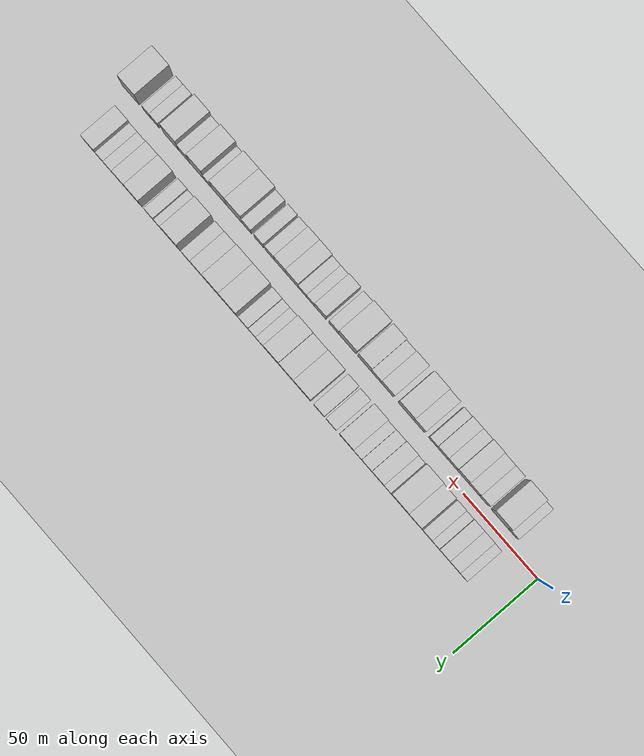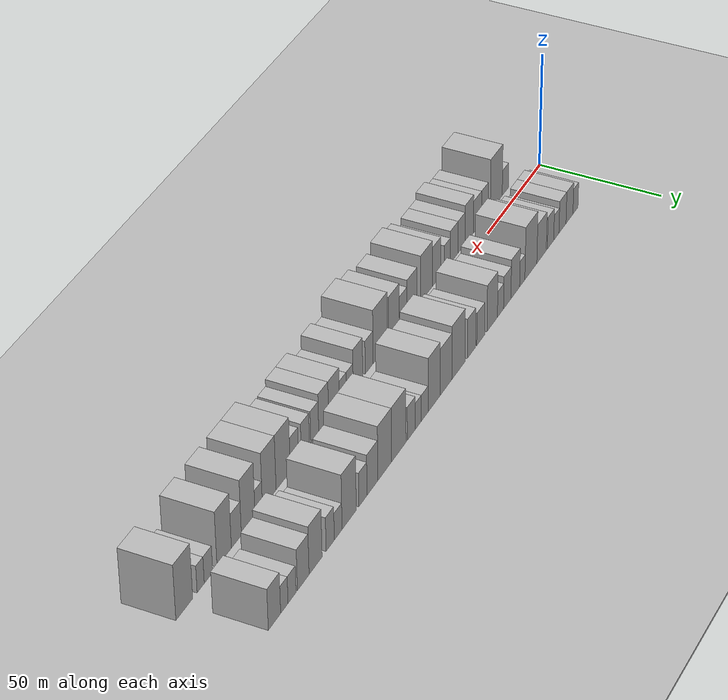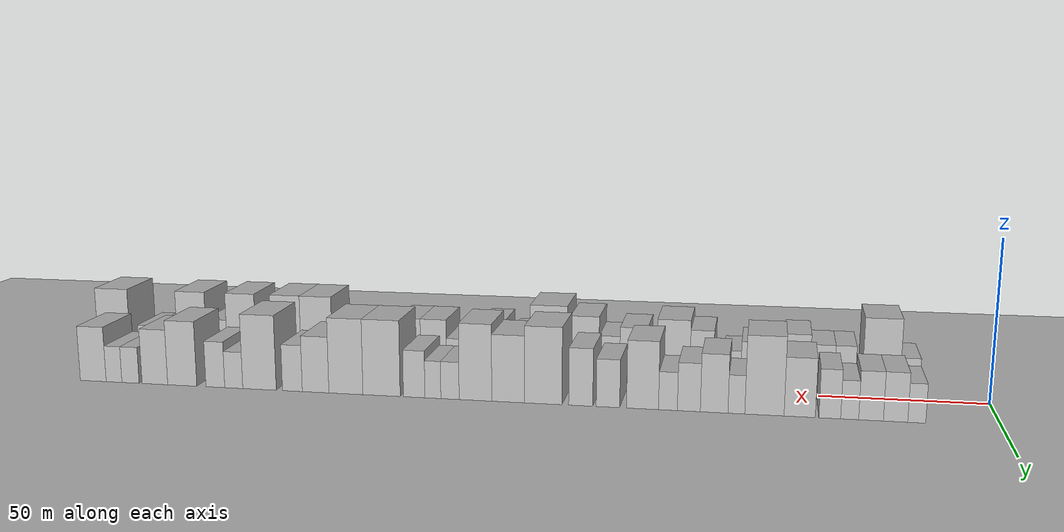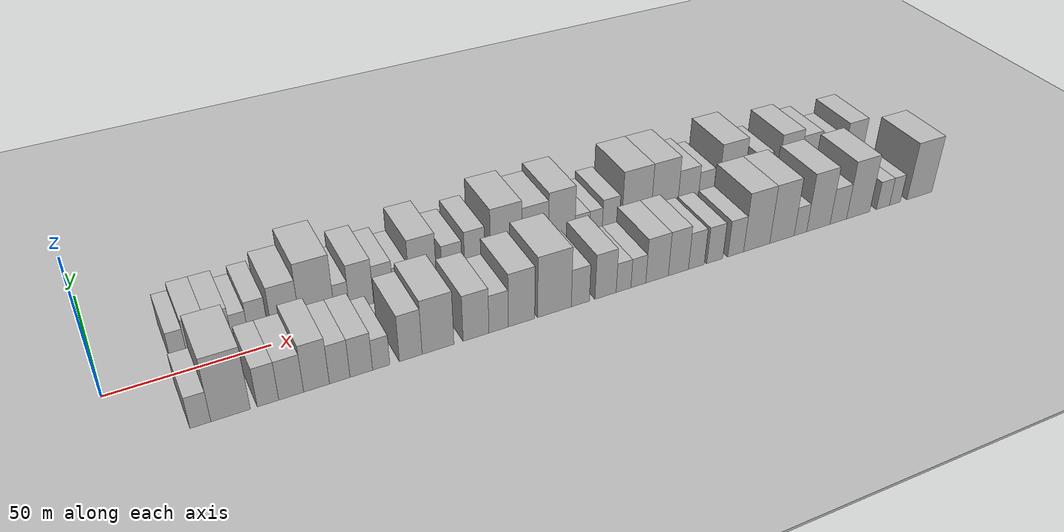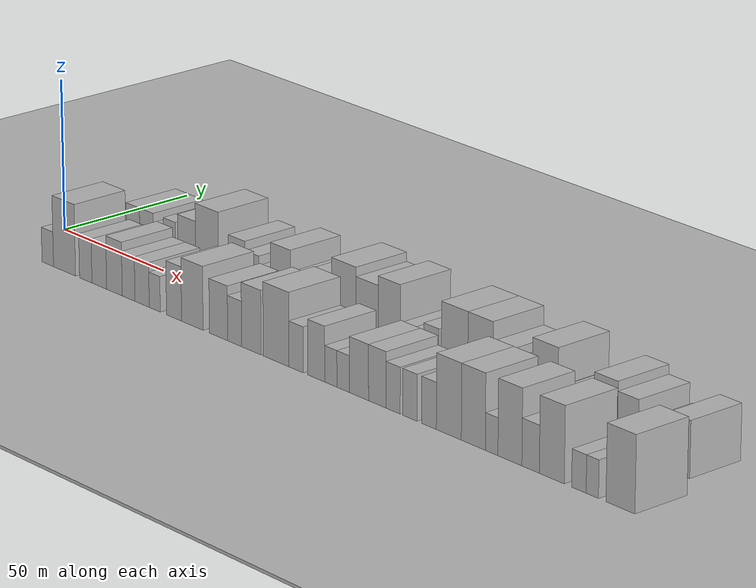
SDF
<?xml version="1.0" encoding="utf-8"?>

<sdf version="1.6">

   <world name="default">

      <gui fullscreen="0">

         <camera name="user_camera">

            <pose>-15 0 4.57585 0 0 0</pose>

            <view_controller>orbit</view_controller>

         </camera>

      </gui>

      <scene>

         <sky>

           <clouds>

             <speed>12</speed>

           </clouds>

         </sky>

         <ambient>0.4 0.4 0.4 1</ambient>

         <background>0.7 0.7 0.7 1</background>

         <shadows>1</shadows>

      </scene>

      <gravity>0 0 -9.8066</gravity>

      <magnetic_field>6e-06 2.3e-05 -4.2e-05</magnetic_field>

      <physics default="0" name="default_physics" type="ode">

         <ode>

            <solver>

               <type>quick</type>

               <iters>10</iters>

               <sor>1.0</sor>

               <use_dynamic_moi_rescaling>0</use_dynamic_moi_rescaling>

            </solver>

            <constraints>

               <cfm>0</cfm>

               <erp>0.2</erp>

               <contact_max_correcting_vel>100</contact_max_correcting_vel>

               <contact_surface_layer>0.001</contact_surface_layer>

            </constraints>

         </ode>

         <max_step_size>0.004</max_step_size>

         <real_time_factor>1</real_time_factor>

         <real_time_update_rate>250</real_time_update_rate>

      </physics>

      <light name="sun" type="directional">

         <cast_shadows>1</cast_shadows>

         <pose>0 0 10 0 0 0</pose>

         <diffuse>0.8 0.8 0.8 1</diffuse>

         <specular>0.2 0.2 0.2 1</specular>

         <attenuation>

            <range>1000</range>

            <constant>0.9</constant>

            <linear>0.01</linear>

            <quadratic>0.001</quadratic>

         </attenuation>

         <direction>-0.5 0.1 -0.9</direction>

      </light>

      <include>

         <name>ground_plane_1</name>

         <uri>model://HANNAS_ground_plane</uri>

         <pose>0 0 0  0 0 0</pose>

      </include>

      <include>

         <name>ground_plane_2</name>

         <uri>model://HANNAS_ground_plane</uri>

         <pose>100 0 0  0 0 0</pose>

      </include>

      <model name="building_1">

         <static>1</static>

         <pose frame="">23.4650 14.5000 0 0.000000 0.000000 1.570796</pose>

         <link name="link">

            <pose frame="">0 0 6.00 0 0 0</pose>

            <collision name="collision">

               <geometry>

                  <box>

                     <size>20.0000 4.9301 12.0000</size>

                  </box>

               </geometry>

               <max_contacts>10</max_contacts>

               <surface>

                  <contact>

                     <ode/>

                  </contact>

                  <bounce/>

                  <friction>

                     <torsional>

                        <ode/>

                     </torsional>

                     <ode/>

                  </friction>

               </surface>

            </collision>

            <visual name="visual">

               <cast_shadows>0</cast_shadows>

               <geometry>

                  <box>

                     <size>20.0000 4.9301 12.0000</size>

                  </box>

               </geometry>

               <material>

                  <script>

                     <uri>model://HANNAS_wall/materials/scripts</uri>

                     <uri>model://HANNAS_wall/materials/textures</uri>

                     <name>vrc/HANNAS_wall</name>

                  </script>

               </material>

            </visual>

            <self_collide>0</self_collide>

            <enable_wind>0</enable_wind>

            <kinematic>0</kinematic>

         </link>

      </model>

      <model name="building_2">

         <static>1</static>

         <pose frame="">29.2978 14.5000 0 0.000000 0.000000 1.570796</pose>

         <link name="link">

            <pose frame="">0 0 7.50 0 0 0</pose>

            <collision name="collision">

               <geometry>

                  <box>

                     <size>20.0000 6.7355 15.0000</size>

                  </box>

               </geometry>

               <max_contacts>10</max_contacts>

               <surface>

                  <contact>

                     <ode/>

                  </contact>

                  <bounce/>

                  <friction>

                     <torsional>

                        <ode/>

                     </torsional>

                     <ode/>

                  </friction>

               </surface>

            </collision>

            <visual name="visual">

               <cast_shadows>0</cast_shadows>

               <geometry>

                  <box>

                     <size>20.0000 6.7355 15.0000</size>

                  </box>

               </geometry>

               <material>

                  <script>

                     <uri>model://HANNAS_wall/materials/scripts</uri>

                     <uri>model://HANNAS_wall/materials/textures</uri>

                     <name>vrc/HANNAS_wall</name>

                  </script>

               </material>

            </visual>

            <self_collide>0</self_collide>

            <enable_wind>0</enable_wind>

            <kinematic>0</kinematic>

         </link>

      </model>

      <model name="building_3">

         <static>1</static>

         <pose frame="">36.0947 14.5000 0 0.000000 0.000000 1.570796</pose>

         <link name="link">

            <pose frame="">0 0 7.50 0 0 0</pose>

            <collision name="collision">

               <geometry>

                  <box>

                     <size>20.0000 6.8582 15.0000</size>

                  </box>

               </geometry>

               <max_contacts>10</max_contacts>

               <surface>

                  <contact>

                     <ode/>

                  </contact>

                  <bounce/>

                  <friction>

                     <torsional>

                        <ode/>

                     </torsional>

                     <ode/>

                  </friction>

               </surface>

            </collision>

            <visual name="visual">

               <cast_shadows>0</cast_shadows>

               <geometry>

                  <box>

                     <size>20.0000 6.8582 15.0000</size>

                  </box>

               </geometry>

               <material>

                  <script>

                     <uri>model://HANNAS_wall/materials/scripts</uri>

                     <uri>model://HANNAS_wall/materials/textures</uri>

                     <name>vrc/HANNAS_wall</name>

                  </script>

               </material>

            </visual>

            <self_collide>0</self_collide>

            <enable_wind>0</enable_wind>

            <kinematic>0</kinematic>

         </link>

      </model>

      <model name="building_4">

         <static>1</static>

         <pose frame="">42.0374 14.5000 0 0.000000 0.000000 1.570796</pose>

         <link name="link">

            <pose frame="">0 0 6.00 0 0 0</pose>

            <collision name="collision">

               <geometry>

                  <box>

                     <size>20.0000 5.0272 12.0000</size>

                  </box>

               </geometry>

               <max_contacts>10</max_contacts>

               <surface>

                  <contact>

                     <ode/>

                  </contact>

                  <bounce/>

                  <friction>

                     <torsional>

                        <ode/>

                     </torsional>

                     <ode/>

                  </friction>

               </surface>

            </collision>

            <visual name="visual">

               <cast_shadows>0</cast_shadows>

               <geometry>

                  <box>

                     <size>20.0000 5.0272 12.0000</size>

                  </box>

               </geometry>

               <material>

                  <script>

                     <uri>model://HANNAS_wall/materials/scripts</uri>

                     <uri>model://HANNAS_wall/materials/textures</uri>

                     <name>vrc/HANNAS_wall</name>

                  </script>

               </material>

            </visual>

            <self_collide>0</self_collide>

            <enable_wind>0</enable_wind>

            <kinematic>0</kinematic>

         </link>

      </model>

      <model name="building_5">

         <static>1</static>

         <pose frame="">47.6003 14.5000 0 0.000000 0.000000 1.570796</pose>

         <link name="link">

            <pose frame="">0 0 7.50 0 0 0</pose>

            <collision name="collision">

               <geometry>

                  <box>

                     <size>20.0000 6.0985 15.0000</size>

                  </box>

               </geometry>

               <max_contacts>10</max_contacts>

               <surface>

                  <contact>

                     <ode/>

                  </contact>

                  <bounce/>

                  <friction>

                     <torsional>

                        <ode/>

                     </torsional>

                     <ode/>

                  </friction>

               </surface>

            </collision>

            <visual name="visual">

               <cast_shadows>0</cast_shadows>

               <geometry>

                  <box>

                     <size>20.0000 6.0985 15.0000</size>

                  </box>

               </geometry>

               <material>

                  <script>

                     <uri>model://HANNAS_wall/materials/scripts</uri>

                     <uri>model://HANNAS_wall/materials/textures</uri>

                     <name>vrc/HANNAS_wall</name>

                  </script>

               </material>

            </visual>

            <self_collide>0</self_collide>

            <enable_wind>0</enable_wind>

            <kinematic>0</kinematic>

         </link>

      </model>

      <model name="building_6">

         <static>1</static>

         <pose frame="">56.0655 14.5000 0 0.000000 0.000000 1.570796</pose>

         <link name="link">

            <pose frame="">0 0 9.00 0 0 0</pose>

            <collision name="collision">

               <geometry>

                  <box>

                     <size>20.0000 8.8320 18.0000</size>

                  </box>

               </geometry>

               <max_contacts>10</max_contacts>

               <surface>

                  <contact>

                     <ode/>

                  </contact>

                  <bounce/>

                  <friction>

                     <torsional>

                        <ode/>

                     </torsional>

                     <ode/>

                  </friction>

               </surface>

            </collision>

            <visual name="visual">

               <cast_shadows>0</cast_shadows>

               <geometry>

                  <box>

                     <size>20.0000 8.8320 18.0000</size>

                  </box>

               </geometry>

               <material>

                  <script>

                     <uri>model://HANNAS_wall/materials/scripts</uri>

                     <uri>model://HANNAS_wall/materials/textures</uri>

                     <name>vrc/HANNAS_wall</name>

                  </script>

               </material>

            </visual>

            <self_collide>0</self_collide>

            <enable_wind>0</enable_wind>

            <kinematic>0</kinematic>

         </link>

      </model>

      <model name="building_7">

         <static>1</static>

         <pose frame="">66.0699 14.5000 0 0.000000 0.000000 1.570796</pose>

         <link name="link">

            <pose frame="">0 0 12.00 0 0 0</pose>

            <collision name="collision">

               <geometry>

                  <box>

                     <size>20.0000 11.1767 24.0000</size>

                  </box>

               </geometry>

               <max_contacts>10</max_contacts>

               <surface>

                  <contact>

                     <ode/>

                  </contact>

                  <bounce/>

                  <friction>

                     <torsional>

                        <ode/>

                     </torsional>

                     <ode/>

                  </friction>

               </surface>

            </collision>

            <visual name="visual">

               <cast_shadows>0</cast_shadows>

               <geometry>

                  <box>

                     <size>20.0000 11.1767 24.0000</size>

                  </box>

               </geometry>

               <material>

                  <script>

                     <uri>model://HANNAS_wall/materials/scripts</uri>

                     <uri>model://HANNAS_wall/materials/textures</uri>

                     <name>vrc/HANNAS_wall</name>

                  </script>

               </material>

            </visual>

            <self_collide>0</self_collide>

            <enable_wind>0</enable_wind>

            <kinematic>0</kinematic>

         </link>

      </model>

      <model name="building_8">

         <static>1</static>

         <pose frame="">74.0751 14.5000 0 0.000000 0.000000 1.570796</pose>

         <link name="link">

            <pose frame="">0 0 6.00 0 0 0</pose>

            <collision name="collision">

               <geometry>

                  <box>

                     <size>20.0000 4.8337 12.0000</size>

                  </box>

               </geometry>

               <max_contacts>10</max_contacts>

               <surface>

                  <contact>

                     <ode/>

                  </contact>

                  <bounce/>

                  <friction>

                     <torsional>

                        <ode/>

                     </torsional>

                     <ode/>

                  </friction>

               </surface>

            </collision>

            <visual name="visual">

               <cast_shadows>0</cast_shadows>

               <geometry>

                  <box>

                     <size>20.0000 4.8337 12.0000</size>

                  </box>

               </geometry>

               <material>

                  <script>

                     <uri>model://HANNAS_wall/materials/scripts</uri>

                     <uri>model://HANNAS_wall/materials/textures</uri>

                     <name>vrc/HANNAS_wall</name>

                  </script>

               </material>

            </visual>

            <self_collide>0</self_collide>

            <enable_wind>0</enable_wind>

            <kinematic>0</kinematic>

         </link>

      </model>

      <model name="building_9">

         <static>1</static>

         <pose frame="">80.4872 14.5000 0 0.000000 0.000000 1.570796</pose>

         <link name="link">

            <pose frame="">0 0 9.00 0 0 0</pose>

            <collision name="collision">

               <geometry>

                  <box>

                     <size>20.0000 7.9904 18.0000</size>

                  </box>

               </geometry>

               <max_contacts>10</max_contacts>

               <surface>

                  <contact>

                     <ode/>

                  </contact>

                  <bounce/>

                  <friction>

                     <torsional>

                        <ode/>

                     </torsional>

                     <ode/>

                  </friction>

               </surface>

            </collision>

            <visual name="visual">

               <cast_shadows>0</cast_shadows>

               <geometry>

                  <box>

                     <size>20.0000 7.9904 18.0000</size>

                  </box>

               </geometry>

               <material>

                  <script>

                     <uri>model://HANNAS_wall/materials/scripts</uri>

                     <uri>model://HANNAS_wall/materials/textures</uri>

                     <name>vrc/HANNAS_wall</name>

                  </script>

               </material>

            </visual>

            <self_collide>0</self_collide>

            <enable_wind>0</enable_wind>

            <kinematic>0</kinematic>

         </link>

      </model>

      <model name="building_10">

         <static>1</static>

         <pose frame="">87.8059 14.5000 0 0.000000 0.000000 1.570796</pose>

         <link name="link">

            <pose frame="">0 0 7.50 0 0 0</pose>

            <collision name="collision">

               <geometry>

                  <box>

                     <size>20.0000 6.6469 15.0000</size>

                  </box>

               </geometry>

               <max_contacts>10</max_contacts>

               <surface>

                  <contact>

                     <ode/>

                  </contact>

                  <bounce/>

                  <friction>

                     <torsional>

                        <ode/>

                     </torsional>

                     <ode/>

                  </friction>

               </surface>

            </collision>

            <visual name="visual">

               <cast_shadows>0</cast_shadows>

               <geometry>

                  <box>

                     <size>20.0000 6.6469 15.0000</size>

                  </box>

               </geometry>

               <material>

                  <script>

                     <uri>model://HANNAS_wall/materials/scripts</uri>

                     <uri>model://HANNAS_wall/materials/textures</uri>

                     <name>vrc/HANNAS_wall</name>

                  </script>

               </material>

            </visual>

            <self_collide>0</self_collide>

            <enable_wind>0</enable_wind>

            <kinematic>0</kinematic>

         </link>

      </model>

      <model name="building_11">

         <static>1</static>

         <pose frame="">93.8801 14.5000 0 0.000000 0.000000 1.570796</pose>

         <link name="link">

            <pose frame="">0 0 6.00 0 0 0</pose>

            <collision name="collision">

               <geometry>

                  <box>

                     <size>20.0000 5.5015 12.0000</size>

                  </box>

               </geometry>

               <max_contacts>10</max_contacts>

               <surface>

                  <contact>

                     <ode/>

                  </contact>

                  <bounce/>

                  <friction>

                     <torsional>

                        <ode/>

                     </torsional>

                     <ode/>

                  </friction>

               </surface>

            </collision>

            <visual name="visual">

               <cast_shadows>0</cast_shadows>

               <geometry>

                  <box>

                     <size>20.0000 5.5015 12.0000</size>

                  </box>

               </geometry>

               <material>

                  <script>

                     <uri>model://HANNAS_wall/materials/scripts</uri>

                     <uri>model://HANNAS_wall/materials/textures</uri>

                     <name>vrc/HANNAS_wall</name>

                  </script>

               </material>

            </visual>

            <self_collide>0</self_collide>

            <enable_wind>0</enable_wind>

            <kinematic>0</kinematic>

         </link>

      </model>

      <model name="building_12">

         <static>1</static>

         <pose frame="">101.3235 14.5000 0 0.000000 0.000000 1.570796</pose>

         <link name="link">

            <pose frame="">0 0 10.50 0 0 0</pose>

            <collision name="collision">

               <geometry>

                  <box>

                     <size>20.0000 9.3853 21.0000</size>

                  </box>

               </geometry>

               <max_contacts>10</max_contacts>

               <surface>

                  <contact>

                     <ode/>

                  </contact>

                  <bounce/>

                  <friction>

                     <torsional>

                        <ode/>

                     </torsional>

                     <ode/>

                  </friction>

               </surface>

            </collision>

            <visual name="visual">

               <cast_shadows>0</cast_shadows>

               <geometry>

                  <box>

                     <size>20.0000 9.3853 21.0000</size>

                  </box>

               </geometry>

               <material>

                  <script>

                     <uri>model://HANNAS_wall/materials/scripts</uri>

                     <uri>model://HANNAS_wall/materials/textures</uri>

                     <name>vrc/HANNAS_wall</name>

                  </script>

               </material>

            </visual>

            <self_collide>0</self_collide>

            <enable_wind>0</enable_wind>

            <kinematic>0</kinematic>

         </link>

      </model>

      <model name="building_13">

         <static>1</static>

         <pose frame="">111.5054 14.5000 0 0.000000 0.000000 1.570796</pose>

         <link name="link">

            <pose frame="">0 0 7.50 0 0 0</pose>

            <collision name="collision">

               <geometry>

                  <box>

                     <size>20.0000 6.9785 15.0000</size>

                  </box>

               </geometry>

               <max_contacts>10</max_contacts>

               <surface>

                  <contact>

                     <ode/>

                  </contact>

                  <bounce/>

                  <friction>

                     <torsional>

                        <ode/>

                     </torsional>

                     <ode/>

                  </friction>

               </surface>

            </collision>

            <visual name="visual">

               <cast_shadows>0</cast_shadows>

               <geometry>

                  <box>

                     <size>20.0000 6.9785 15.0000</size>

                  </box>

               </geometry>

               <material>

                  <script>

                     <uri>model://HANNAS_wall/materials/scripts</uri>

                     <uri>model://HANNAS_wall/materials/textures</uri>

                     <name>vrc/HANNAS_wall</name>

                  </script>

               </material>

            </visual>

            <self_collide>0</self_collide>

            <enable_wind>0</enable_wind>

            <kinematic>0</kinematic>

         </link>

      </model>

      <model name="building_14">

         <static>1</static>

         <pose frame="">119.5979 14.5000 0 0.000000 0.000000 1.570796</pose>

         <link name="link">

            <pose frame="">0 0 9.00 0 0 0</pose>

            <collision name="collision">

               <geometry>

                  <box>

                     <size>20.0000 7.2065 18.0000</size>

                  </box>

               </geometry>

               <max_contacts>10</max_contacts>

               <surface>

                  <contact>

                     <ode/>

                  </contact>

                  <bounce/>

                  <friction>

                     <torsional>

                        <ode/>

                     </torsional>

                     <ode/>

                  </friction>

               </surface>

            </collision>

            <visual name="visual">

               <cast_shadows>0</cast_shadows>

               <geometry>

                  <box>

                     <size>20.0000 7.2065 18.0000</size>

                  </box>

               </geometry>

               <material>

                  <script>

                     <uri>model://HANNAS_wall/materials/scripts</uri>

                     <uri>model://HANNAS_wall/materials/textures</uri>

                     <name>vrc/HANNAS_wall</name>

                  </script>

               </material>

            </visual>

            <self_collide>0</self_collide>

            <enable_wind>0</enable_wind>

            <kinematic>0</kinematic>

         </link>

      </model>

      <model name="building_15">

         <static>1</static>

         <pose frame="">130.8828 14.5000 0 0.000000 0.000000 1.570796</pose>

         <link name="link">

            <pose frame="">0 0 12.00 0 0 0</pose>

            <collision name="collision">

               <geometry>

                  <box>

                     <size>20.0000 11.3635 24.0000</size>

                  </box>

               </geometry>

               <max_contacts>10</max_contacts>

               <surface>

                  <contact>

                     <ode/>

                  </contact>

                  <bounce/>

                  <friction>

                     <torsional>

                        <ode/>

                     </torsional>

                     <ode/>

                  </friction>

               </surface>

            </collision>

            <visual name="visual">

               <cast_shadows>0</cast_shadows>

               <geometry>

                  <box>

                     <size>20.0000 11.3635 24.0000</size>

                  </box>

               </geometry>

               <material>

                  <script>

                     <uri>model://HANNAS_wall/materials/scripts</uri>

                     <uri>model://HANNAS_wall/materials/textures</uri>

                     <name>vrc/HANNAS_wall</name>

                  </script>

               </material>

            </visual>

            <self_collide>0</self_collide>

            <enable_wind>0</enable_wind>

            <kinematic>0</kinematic>

         </link>

      </model>

      <model name="building_16">

         <static>1</static>

         <pose frame="">141.5021 14.5000 0 0.000000 0.000000 1.570796</pose>

         <link name="link">

            <pose frame="">0 0 10.50 0 0 0</pose>

            <collision name="collision">

               <geometry>

                  <box>

                     <size>20.0000 9.8750 21.0000</size>

                  </box>

               </geometry>

               <max_contacts>10</max_contacts>

               <surface>

                  <contact>

                     <ode/>

                  </contact>

                  <bounce/>

                  <friction>

                     <torsional>

                        <ode/>

                     </torsional>

                     <ode/>

                  </friction>

               </surface>

            </collision>

            <visual name="visual">

               <cast_shadows>0</cast_shadows>

               <geometry>

                  <box>

                     <size>20.0000 9.8750 21.0000</size>

                  </box>

               </geometry>

               <material>

                  <script>

                     <uri>model://HANNAS_wall/materials/scripts</uri>

                     <uri>model://HANNAS_wall/materials/textures</uri>

                     <name>vrc/HANNAS_wall</name>

                  </script>

               </material>

            </visual>

            <self_collide>0</self_collide>

            <enable_wind>0</enable_wind>

            <kinematic>0</kinematic>

         </link>

      </model>

      <model name="building_17">

         <static>1</static>

         <pose frame="">151.4321 14.5000 0 0.000000 0.000000 1.570796</pose>

         <link name="link">

            <pose frame="">0 0 12.00 0 0 0</pose>

            <collision name="collision">

               <geometry>

                  <box>

                     <size>20.0000 9.9852 24.0000</size>

                  </box>

               </geometry>

               <max_contacts>10</max_contacts>

               <surface>

                  <contact>

                     <ode/>

                  </contact>

                  <bounce/>

                  <friction>

                     <torsional>

                        <ode/>

                     </torsional>

                     <ode/>

                  </friction>

               </surface>

            </collision>

            <visual name="visual">

               <cast_shadows>0</cast_shadows>

               <geometry>

                  <box>

                     <size>20.0000 9.9852 24.0000</size>

                  </box>

               </geometry>

               <material>

                  <script>

                     <uri>model://HANNAS_wall/materials/scripts</uri>

                     <uri>model://HANNAS_wall/materials/textures</uri>

                     <name>vrc/HANNAS_wall</name>

                  </script>

               </material>

            </visual>

            <self_collide>0</self_collide>

            <enable_wind>0</enable_wind>

            <kinematic>0</kinematic>

         </link>

      </model>

      <model name="building_18">

         <static>1</static>

         <pose frame="">159.2347 14.5000 0 0.000000 0.000000 1.570796</pose>

         <link name="link">

            <pose frame="">0 0 6.00 0 0 0</pose>

            <collision name="collision">

               <geometry>

                  <box>

                     <size>20.0000 5.6200 12.0000</size>

                  </box>

               </geometry>

               <max_contacts>10</max_contacts>

               <surface>

                  <contact>

                     <ode/>

                  </contact>

                  <bounce/>

                  <friction>

                     <torsional>

                        <ode/>

                     </torsional>

                     <ode/>

                  </friction>

               </surface>

            </collision>

            <visual name="visual">

               <cast_shadows>0</cast_shadows>

               <geometry>

                  <box>

                     <size>20.0000 5.6200 12.0000</size>

                  </box>

               </geometry>

               <material>

                  <script>

                     <uri>model://HANNAS_wall/materials/scripts</uri>

                     <uri>model://HANNAS_wall/materials/textures</uri>

                     <name>vrc/HANNAS_wall</name>

                  </script>

               </material>

            </visual>

            <self_collide>0</self_collide>

            <enable_wind>0</enable_wind>

            <kinematic>0</kinematic>

         </link>

      </model>

      <model name="building_19">

         <static>1</static>

         <pose frame="">164.5146 14.5000 0 0.000000 0.000000 1.570796</pose>

         <link name="link">

            <pose frame="">0 0 6.00 0 0 0</pose>

            <collision name="collision">

               <geometry>

                  <box>

                     <size>20.0000 4.9398 12.0000</size>

                  </box>

               </geometry>

               <max_contacts>10</max_contacts>

               <surface>

                  <contact>

                     <ode/>

                  </contact>

                  <bounce/>

                  <friction>

                     <torsional>

                        <ode/>

                     </torsional>

                     <ode/>

                  </friction>

               </surface>

            </collision>

            <visual name="visual">

               <cast_shadows>0</cast_shadows>

               <geometry>

                  <box>

                     <size>20.0000 4.9398 12.0000</size>

                  </box>

               </geometry>

               <material>

                  <script>

                     <uri>model://HANNAS_wall/materials/scripts</uri>

                     <uri>model://HANNAS_wall/materials/textures</uri>

                     <name>vrc/HANNAS_wall</name>

                  </script>

               </material>

            </visual>

            <self_collide>0</self_collide>

            <enable_wind>0</enable_wind>

            <kinematic>0</kinematic>

         </link>

      </model>

      <model name="building_20">

         <static>1</static>

         <pose frame="">170.3260 14.5000 0 0.000000 0.000000 1.570796</pose>

         <link name="link">

            <pose frame="">0 0 7.50 0 0 0</pose>

            <collision name="collision">

               <geometry>

                  <box>

                     <size>20.0000 6.6828 15.0000</size>

                  </box>

               </geometry>

               <max_contacts>10</max_contacts>

               <surface>

                  <contact>

                     <ode/>

                  </contact>

                  <bounce/>

                  <friction>

                     <torsional>

                        <ode/>

                     </torsional>

                     <ode/>

                  </friction>

               </surface>

            </collision>

            <visual name="visual">

               <cast_shadows>0</cast_shadows>

               <geometry>

                  <box>

                     <size>20.0000 6.6828 15.0000</size>

                  </box>

               </geometry>

               <material>

                  <script>

                     <uri>model://HANNAS_wall/materials/scripts</uri>

                     <uri>model://HANNAS_wall/materials/textures</uri>

                     <name>vrc/HANNAS_wall</name>

                  </script>

               </material>

            </visual>

            <self_collide>0</self_collide>

            <enable_wind>0</enable_wind>

            <kinematic>0</kinematic>

         </link>

      </model>

      <model name="building_21">

         <static>1</static>

         <pose frame="">180.5012 14.5000 0 0.000000 0.000000 1.570796</pose>

         <link name="link">

            <pose frame="">0 0 12.00 0 0 0</pose>

            <collision name="collision">

               <geometry>

                  <box>

                     <size>20.0000 11.6677 24.0000</size>

                  </box>

               </geometry>

               <max_contacts>10</max_contacts>

               <surface>

                  <contact>

                     <ode/>

                  </contact>

                  <bounce/>

                  <friction>

                     <torsional>

                        <ode/>

                     </torsional>

                     <ode/>

                  </friction>

               </surface>

            </collision>

            <visual name="visual">

               <cast_shadows>0</cast_shadows>

               <geometry>

                  <box>

                     <size>20.0000 11.6677 24.0000</size>

                  </box>

               </geometry>

               <material>

                  <script>

                     <uri>model://HANNAS_wall/materials/scripts</uri>

                     <uri>model://HANNAS_wall/materials/textures</uri>

                     <name>vrc/HANNAS_wall</name>

                  </script>

               </material>

            </visual>

            <self_collide>0</self_collide>

            <enable_wind>0</enable_wind>

            <kinematic>0</kinematic>

         </link>

      </model>

      <model name="building_22">

         <static>1</static>

         <pose frame="">191.7352 14.5000 0 0.000000 0.000000 1.570796</pose>

         <link name="link">

            <pose frame="">0 0 12.00 0 0 0</pose>

            <collision name="collision">

               <geometry>

                  <box>

                     <size>20.0000 10.8002 24.0000</size>

                  </box>

               </geometry>

               <max_contacts>10</max_contacts>

               <surface>

                  <contact>

                     <ode/>

                  </contact>

                  <bounce/>

                  <friction>

                     <torsional>

                        <ode/>

                     </torsional>

                     <ode/>

                  </friction>

               </surface>

            </collision>

            <visual name="visual">

               <cast_shadows>0</cast_shadows>

               <geometry>

                  <box>

                     <size>20.0000 10.8002 24.0000</size>

                  </box>

               </geometry>

               <material>

                  <script>

                     <uri>model://HANNAS_wall/materials/scripts</uri>

                     <uri>model://HANNAS_wall/materials/textures</uri>

                     <name>vrc/HANNAS_wall</name>

                  </script>

               </material>

            </visual>

            <self_collide>0</self_collide>

            <enable_wind>0</enable_wind>

            <kinematic>0</kinematic>

         </link>

      </model>

      <model name="building_23">

         <static>1</static>

         <pose frame="">201.3734 14.5000 0 0.000000 0.000000 1.570796</pose>

         <link name="link">

            <pose frame="">0 0 9.00 0 0 0</pose>

            <collision name="collision">

               <geometry>

                  <box>

                     <size>20.0000 8.4760 18.0000</size>

                  </box>

               </geometry>

               <max_contacts>10</max_contacts>

               <surface>

                  <contact>

                     <ode/>

                  </contact>

                  <bounce/>

                  <friction>

                     <torsional>

                        <ode/>

                     </torsional>

                     <ode/>

                  </friction>

               </surface>

            </collision>

            <visual name="visual">

               <cast_shadows>0</cast_shadows>

               <geometry>

                  <box>

                     <size>20.0000 8.4760 18.0000</size>

                  </box>

               </geometry>

               <material>

                  <script>

                     <uri>model://HANNAS_wall/materials/scripts</uri>

                     <uri>model://HANNAS_wall/materials/textures</uri>

                     <name>vrc/HANNAS_wall</name>

                  </script>

               </material>

            </visual>

            <self_collide>0</self_collide>

            <enable_wind>0</enable_wind>

            <kinematic>0</kinematic>

         </link>

      </model>

      <model name="building_24">

         <static>1</static>

         <pose frame="">208.7909 14.5000 0 0.000000 0.000000 1.570796</pose>

         <link name="link">

            <pose frame="">0 0 7.50 0 0 0</pose>

            <collision name="collision">

               <geometry>

                  <box>

                     <size>20.0000 6.3590 15.0000</size>

                  </box>

               </geometry>

               <max_contacts>10</max_contacts>

               <surface>

                  <contact>

                     <ode/>

                  </contact>

                  <bounce/>

                  <friction>

                     <torsional>

                        <ode/>

                     </torsional>

                     <ode/>

                  </friction>

               </surface>

            </collision>

            <visual name="visual">

               <cast_shadows>0</cast_shadows>

               <geometry>

                  <box>

                     <size>20.0000 6.3590 15.0000</size>

                  </box>

               </geometry>

               <material>

                  <script>

                     <uri>model://HANNAS_wall/materials/scripts</uri>

                     <uri>model://HANNAS_wall/materials/textures</uri>

                     <name>vrc/HANNAS_wall</name>

                  </script>

               </material>

            </visual>

            <self_collide>0</self_collide>

            <enable_wind>0</enable_wind>

            <kinematic>0</kinematic>

         </link>

      </model>

      <model name="building_25">

         <static>1</static>

         <pose frame="">219.3993 14.5000 0 0.000000 0.000000 1.570796</pose>

         <link name="link">

            <pose frame="">0 0 12.00 0 0 0</pose>

            <collision name="collision">

               <geometry>

                  <box>

                     <size>20.0000 10.8577 24.0000</size>

                  </box>

               </geometry>

               <max_contacts>10</max_contacts>

               <surface>

                  <contact>

                     <ode/>

                  </contact>

                  <bounce/>

                  <friction>

                     <torsional>

                        <ode/>

                     </torsional>

                     <ode/>

                  </friction>

               </surface>

            </collision>

            <visual name="visual">

               <cast_shadows>0</cast_shadows>

               <geometry>

                  <box>

                     <size>20.0000 10.8577 24.0000</size>

                  </box>

               </geometry>

               <material>

                  <script>

                     <uri>model://HANNAS_wall/materials/scripts</uri>

                     <uri>model://HANNAS_wall/materials/textures</uri>

                     <name>vrc/HANNAS_wall</name>

                  </script>

               </material>

            </visual>

            <self_collide>0</self_collide>

            <enable_wind>0</enable_wind>

            <kinematic>0</kinematic>

         </link>

      </model>

      <model name="building_26">

         <static>1</static>

         <pose frame="">227.7608 14.5000 0 0.000000 0.000000 1.570796</pose>

         <link name="link">

            <pose frame="">0 0 6.00 0 0 0</pose>

            <collision name="collision">

               <geometry>

                  <box>

                     <size>20.0000 5.8654 12.0000</size>

                  </box>

               </geometry>

               <max_contacts>10</max_contacts>

               <surface>

                  <contact>

                     <ode/>

                  </contact>

                  <bounce/>

                  <friction>

                     <torsional>

                        <ode/>

                     </torsional>

                     <ode/>

                  </friction>

               </surface>

            </collision>

            <visual name="visual">

               <cast_shadows>0</cast_shadows>

               <geometry>

                  <box>

                     <size>20.0000 5.8654 12.0000</size>

                  </box>

               </geometry>

               <material>

                  <script>

                     <uri>model://HANNAS_wall/materials/scripts</uri>

                     <uri>model://HANNAS_wall/materials/textures</uri>

                     <name>vrc/HANNAS_wall</name>

                  </script>

               </material>

            </visual>

            <self_collide>0</self_collide>

            <enable_wind>0</enable_wind>

            <kinematic>0</kinematic>

         </link>

      </model>

      <model name="building_27">

         <static>1</static>

         <pose frame="">233.7735 14.5000 0 0.000000 0.000000 1.570796</pose>

         <link name="link">

            <pose frame="">0 0 7.50 0 0 0</pose>

            <collision name="collision">

               <geometry>

                  <box>

                     <size>20.0000 6.1600 15.0000</size>

                  </box>

               </geometry>

               <max_contacts>10</max_contacts>

               <surface>

                  <contact>

                     <ode/>

                  </contact>

                  <bounce/>

                  <friction>

                     <torsional>

                        <ode/>

                     </torsional>

                     <ode/>

                  </friction>

               </surface>

            </collision>

            <visual name="visual">

               <cast_shadows>0</cast_shadows>

               <geometry>

                  <box>

                     <size>20.0000 6.1600 15.0000</size>

                  </box>

               </geometry>

               <material>

                  <script>

                     <uri>model://HANNAS_wall/materials/scripts</uri>

                     <uri>model://HANNAS_wall/materials/textures</uri>

                     <name>vrc/HANNAS_wall</name>

                  </script>

               </material>

            </visual>

            <self_collide>0</self_collide>

            <enable_wind>0</enable_wind>

            <kinematic>0</kinematic>

         </link>

      </model>

      <model name="building_28">

         <static>1</static>

         <pose frame="">244.6639 14.5000 0 0.000000 0.000000 1.570796</pose>

         <link name="link">

            <pose frame="">0 0 10.50 0 0 0</pose>

            <collision name="collision">

               <geometry>

                  <box>

                     <size>20.0000 9.6207 21.0000</size>

                  </box>

               </geometry>

               <max_contacts>10</max_contacts>

               <surface>

                  <contact>

                     <ode/>

                  </contact>

                  <bounce/>

                  <friction>

                     <torsional>

                        <ode/>

                     </torsional>

                     <ode/>

                  </friction>

               </surface>

            </collision>

            <visual name="visual">

               <cast_shadows>0</cast_shadows>

               <geometry>

                  <box>

                     <size>20.0000 9.6207 21.0000</size>

                  </box>

               </geometry>

               <material>

                  <script>

                     <uri>model://HANNAS_wall/materials/scripts</uri>

                     <uri>model://HANNAS_wall/materials/textures</uri>

                     <name>vrc/HANNAS_wall</name>

                  </script>

               </material>

            </visual>

            <self_collide>0</self_collide>

            <enable_wind>0</enable_wind>

            <kinematic>0</kinematic>

         </link>

      </model>

      <model name="building_29">

         <static>1</static>

         <pose frame="">253.7332 14.5000 0 0.000000 0.000000 1.570796</pose>

         <link name="link">

            <pose frame="">0 0 9.00 0 0 0</pose>

            <collision name="collision">

               <geometry>

                  <box>

                     <size>20.0000 8.5179 18.0000</size>

                  </box>

               </geometry>

               <max_contacts>10</max_contacts>

               <surface>

                  <contact>

                     <ode/>

                  </contact>

                  <bounce/>

                  <friction>

                     <torsional>

                        <ode/>

                     </torsional>

                     <ode/>

                  </friction>

               </surface>

            </collision>

            <visual name="visual">

               <cast_shadows>0</cast_shadows>

               <geometry>

                  <box>

                     <size>20.0000 8.5179 18.0000</size>

                  </box>

               </geometry>

               <material>

                  <script>

                     <uri>model://HANNAS_wall/materials/scripts</uri>

                     <uri>model://HANNAS_wall/materials/textures</uri>

                     <name>vrc/HANNAS_wall</name>

                  </script>

               </material>

            </visual>

            <self_collide>0</self_collide>

            <enable_wind>0</enable_wind>

            <kinematic>0</kinematic>

         </link>

      </model>

      <model name="building_30">

         <static>1</static>

         <pose frame="">261.8812 14.5000 0 0.000000 0.000000 1.570796</pose>

         <link name="link">

            <pose frame="">0 0 6.00 0 0 0</pose>

            <collision name="collision">

               <geometry>

                  <box>

                     <size>20.0000 5.7782 12.0000</size>

                  </box>

               </geometry>

               <max_contacts>10</max_contacts>

               <surface>

                  <contact>

                     <ode/>

                  </contact>

                  <bounce/>

                  <friction>

                     <torsional>

                        <ode/>

                     </torsional>

                     <ode/>

                  </friction>

               </surface>

            </collision>

            <visual name="visual">

               <cast_shadows>0</cast_shadows>

               <geometry>

                  <box>

                     <size>20.0000 5.7782 12.0000</size>

                  </box>

               </geometry>

               <material>

                  <script>

                     <uri>model://HANNAS_wall/materials/scripts</uri>

                     <uri>model://HANNAS_wall/materials/textures</uri>

                     <name>vrc/HANNAS_wall</name>

                  </script>

               </material>

            </visual>

            <self_collide>0</self_collide>

            <enable_wind>0</enable_wind>

            <kinematic>0</kinematic>

         </link>

      </model>

      <model name="building_31">

         <static>1</static>

         <pose frame="">267.4118 14.5000 0 0.000000 0.000000 1.570796</pose>

         <link name="link">

            <pose frame="">0 0 6.00 0 0 0</pose>

            <collision name="collision">

               <geometry>

                  <box>

                     <size>20.0000 5.2829 12.0000</size>

                  </box>

               </geometry>

               <max_contacts>10</max_contacts>

               <surface>

                  <contact>

                     <ode/>

                  </contact>

                  <bounce/>

                  <friction>

                     <torsional>

                        <ode/>

                     </torsional>

                     <ode/>

                  </friction>

               </surface>

            </collision>

            <visual name="visual">

               <cast_shadows>0</cast_shadows>

               <geometry>

                  <box>

                     <size>20.0000 5.2829 12.0000</size>

                  </box>

               </geometry>

               <material>

                  <script>

                     <uri>model://HANNAS_wall/materials/scripts</uri>

                     <uri>model://HANNAS_wall/materials/textures</uri>

                     <name>vrc/HANNAS_wall</name>

                  </script>

               </material>

            </visual>

            <self_collide>0</self_collide>

            <enable_wind>0</enable_wind>

            <kinematic>0</kinematic>

         </link>

      </model>

      <model name="building_32">

         <static>1</static>

         <pose frame="">274.4233 14.5000 0 0.000000 0.000000 1.570796</pose>

         <link name="link">

            <pose frame="">0 0 9.00 0 0 0</pose>

            <collision name="collision">

               <geometry>

                  <box>

                     <size>20.0000 8.7401 18.0000</size>

                  </box>

               </geometry>

               <max_contacts>10</max_contacts>

               <surface>

                  <contact>

                     <ode/>

                  </contact>

                  <bounce/>

                  <friction>

                     <torsional>

                        <ode/>

                     </torsional>

                     <ode/>

                  </friction>

               </surface>

            </collision>

            <visual name="visual">

               <cast_shadows>0</cast_shadows>

               <geometry>

                  <box>

                     <size>20.0000 8.7401 18.0000</size>

                  </box>

               </geometry>

               <material>

                  <script>

                     <uri>model://HANNAS_wall/materials/scripts</uri>

                     <uri>model://HANNAS_wall/materials/textures</uri>

                     <name>vrc/HANNAS_wall</name>

                  </script>

               </material>

            </visual>

            <self_collide>0</self_collide>

            <enable_wind>0</enable_wind>

            <kinematic>0</kinematic>

         </link>

      </model>

      <model name="building_33">

         <static>1</static>

         <pose frame="">22.9316 -14.5000 0 0.000000 0.000000 1.570796</pose>

         <link name="link">

            <pose frame="">0 0 6.00 0 0 0</pose>

            <collision name="collision">

               <geometry>

                  <box>

                     <size>20.0000 5.8632 12.0000</size>

                  </box>

               </geometry>

               <max_contacts>10</max_contacts>

               <surface>

                  <contact>

                     <ode/>

                  </contact>

                  <bounce/>

                  <friction>

                     <torsional>

                        <ode/>

                     </torsional>

                     <ode/>

                  </friction>

               </surface>

            </collision>

            <visual name="visual">

               <cast_shadows>0</cast_shadows>

               <geometry>

                  <box>

                     <size>20.0000 5.8632 12.0000</size>

                  </box>

               </geometry>

               <material>

                  <script>

                     <uri>model://HANNAS_wall/materials/scripts</uri>

                     <uri>model://HANNAS_wall/materials/textures</uri>

                     <name>vrc/HANNAS_wall</name>

                  </script>

               </material>

            </visual>

            <self_collide>0</self_collide>

            <enable_wind>0</enable_wind>

            <kinematic>0</kinematic>

         </link>

      </model>

      <model name="building_34">

         <static>1</static>

         <pose frame="">31.4618 -14.5000 0 0.000000 0.000000 1.570796</pose>

         <link name="link">

            <pose frame="">0 0 12.00 0 0 0</pose>

            <collision name="collision">

               <geometry>

                  <box>

                     <size>20.0000 11.1972 24.0000</size>

                  </box>

               </geometry>

               <max_contacts>10</max_contacts>

               <surface>

                  <contact>

                     <ode/>

                  </contact>

                  <bounce/>

                  <friction>

                     <torsional>

                        <ode/>

                     </torsional>

                     <ode/>

                  </friction>

               </surface>

            </collision>

            <visual name="visual">

               <cast_shadows>0</cast_shadows>

               <geometry>

                  <box>

                     <size>20.0000 11.1972 24.0000</size>

                  </box>

               </geometry>

               <material>

                  <script>

                     <uri>model://HANNAS_wall/materials/scripts</uri>

                     <uri>model://HANNAS_wall/materials/textures</uri>

                     <name>vrc/HANNAS_wall</name>

                  </script>

               </material>

            </visual>

            <self_collide>0</self_collide>

            <enable_wind>0</enable_wind>

            <kinematic>0</kinematic>

         </link>

      </model>

      <model name="building_35">

         <static>1</static>

         <pose frame="">42.1840 -14.5000 0 0.000000 0.000000 1.570796</pose>

         <link name="link">

            <pose frame="">0 0 7.50 0 0 0</pose>

            <collision name="collision">

               <geometry>

                  <box>

                     <size>20.0000 6.2473 15.0000</size>

                  </box>

               </geometry>

               <max_contacts>10</max_contacts>

               <surface>

                  <contact>

                     <ode/>

                  </contact>

                  <bounce/>

                  <friction>

                     <torsional>

                        <ode/>

                     </torsional>

                     <ode/>

                  </friction>

               </surface>

            </collision>

            <visual name="visual">

               <cast_shadows>0</cast_shadows>

               <geometry>

                  <box>

                     <size>20.0000 6.2473 15.0000</size>

                  </box>

               </geometry>

               <material>

                  <script>

                     <uri>model://HANNAS_wall/materials/scripts</uri>

                     <uri>model://HANNAS_wall/materials/textures</uri>

                     <name>vrc/HANNAS_wall</name>

                  </script>

               </material>

            </visual>

            <self_collide>0</self_collide>

            <enable_wind>0</enable_wind>

            <kinematic>0</kinematic>

         </link>

      </model>

      <model name="building_36">

         <static>1</static>

         <pose frame="">48.9838 -14.5000 0 0.000000 0.000000 1.570796</pose>

         <link name="link">

            <pose frame="">0 0 7.50 0 0 0</pose>

            <collision name="collision">

               <geometry>

                  <box>

                     <size>20.0000 7.3523 15.0000</size>

                  </box>

               </geometry>

               <max_contacts>10</max_contacts>

               <surface>

                  <contact>

                     <ode/>

                  </contact>

                  <bounce/>

                  <friction>

                     <torsional>

                        <ode/>

                     </torsional>

                     <ode/>

                  </friction>

               </surface>

            </collision>

            <visual name="visual">

               <cast_shadows>0</cast_shadows>

               <geometry>

                  <box>

                     <size>20.0000 7.3523 15.0000</size>

                  </box>

               </geometry>

               <material>

                  <script>

                     <uri>model://HANNAS_wall/materials/scripts</uri>

                     <uri>model://HANNAS_wall/materials/textures</uri>

                     <name>vrc/HANNAS_wall</name>

                  </script>

               </material>

            </visual>

            <self_collide>0</self_collide>

            <enable_wind>0</enable_wind>

            <kinematic>0</kinematic>

         </link>

      </model>

      <model name="building_37">

         <static>1</static>

         <pose frame="">56.5193 -14.5000 0 0.000000 0.000000 1.570796</pose>

         <link name="link">

            <pose frame="">0 0 9.00 0 0 0</pose>

            <collision name="collision">

               <geometry>

                  <box>

                     <size>20.0000 7.7187 18.0000</size>

                  </box>

               </geometry>

               <max_contacts>10</max_contacts>

               <surface>

                  <contact>

                     <ode/>

                  </contact>

                  <bounce/>

                  <friction>

                     <torsional>

                        <ode/>

                     </torsional>

                     <ode/>

                  </friction>

               </surface>

            </collision>

            <visual name="visual">

               <cast_shadows>0</cast_shadows>

               <geometry>

                  <box>

                     <size>20.0000 7.7187 18.0000</size>

                  </box>

               </geometry>

               <material>

                  <script>

                     <uri>model://HANNAS_wall/materials/scripts</uri>

                     <uri>model://HANNAS_wall/materials/textures</uri>

                     <name>vrc/HANNAS_wall</name>

                  </script>

               </material>

            </visual>

            <self_collide>0</self_collide>

            <enable_wind>0</enable_wind>

            <kinematic>0</kinematic>

         </link>

      </model>

      <model name="building_38">

         <static>1</static>

         <pose frame="">63.5209 -14.5000 0 0.000000 0.000000 1.570796</pose>

         <link name="link">

            <pose frame="">0 0 7.50 0 0 0</pose>

            <collision name="collision">

               <geometry>

                  <box>

                     <size>20.0000 6.2843 15.0000</size>

                  </box>

               </geometry>

               <max_contacts>10</max_contacts>

               <surface>

                  <contact>

                     <ode/>

                  </contact>

                  <bounce/>

                  <friction>

                     <torsional>

                        <ode/>

                     </torsional>

                     <ode/>

                  </friction>

               </surface>

            </collision>

            <visual name="visual">

               <cast_shadows>0</cast_shadows>

               <geometry>

                  <box>

                     <size>20.0000 6.2843 15.0000</size>

                  </box>

               </geometry>

               <material>

                  <script>

                     <uri>model://HANNAS_wall/materials/scripts</uri>

                     <uri>model://HANNAS_wall/materials/textures</uri>

                     <name>vrc/HANNAS_wall</name>

                  </script>

               </material>

            </visual>

            <self_collide>0</self_collide>

            <enable_wind>0</enable_wind>

            <kinematic>0</kinematic>

         </link>

      </model>

      <model name="building_39">

         <static>1</static>

         <pose frame="">70.1465 -14.5000 0 0.000000 0.000000 1.570796</pose>

         <link name="link">

            <pose frame="">0 0 7.50 0 0 0</pose>

            <collision name="collision">

               <geometry>

                  <box>

                     <size>20.0000 6.9668 15.0000</size>

                  </box>

               </geometry>

               <max_contacts>10</max_contacts>

               <surface>

                  <contact>

                     <ode/>

                  </contact>

                  <bounce/>

                  <friction>

                     <torsional>

                        <ode/>

                     </torsional>

                     <ode/>

                  </friction>

               </surface>

            </collision>

            <visual name="visual">

               <cast_shadows>0</cast_shadows>

               <geometry>

                  <box>

                     <size>20.0000 6.9668 15.0000</size>

                  </box>

               </geometry>

               <material>

                  <script>

                     <uri>model://HANNAS_wall/materials/scripts</uri>

                     <uri>model://HANNAS_wall/materials/textures</uri>

                     <name>vrc/HANNAS_wall</name>

                  </script>

               </material>

            </visual>

            <self_collide>0</self_collide>

            <enable_wind>0</enable_wind>

            <kinematic>0</kinematic>

         </link>

      </model>

      <model name="building_40">

         <static>1</static>

         <pose frame="">76.3278 -14.5000 0 0.000000 0.000000 1.570796</pose>

         <link name="link">

            <pose frame="">0 0 6.00 0 0 0</pose>

            <collision name="collision">

               <geometry>

                  <box>

                     <size>20.0000 5.3959 12.0000</size>

                  </box>

               </geometry>

               <max_contacts>10</max_contacts>

               <surface>

                  <contact>

                     <ode/>

                  </contact>

                  <bounce/>

                  <friction>

                     <torsional>

                        <ode/>

                     </torsional>

                     <ode/>

                  </friction>

               </surface>

            </collision>

            <visual name="visual">

               <cast_shadows>0</cast_shadows>

               <geometry>

                  <box>

                     <size>20.0000 5.3959 12.0000</size>

                  </box>

               </geometry>

               <material>

                  <script>

                     <uri>model://HANNAS_wall/materials/scripts</uri>

                     <uri>model://HANNAS_wall/materials/textures</uri>

                     <name>vrc/HANNAS_wall</name>

                  </script>

               </material>

            </visual>

            <self_collide>0</self_collide>

            <enable_wind>0</enable_wind>

            <kinematic>0</kinematic>

         </link>

      </model>

      <model name="building_41">

         <static>1</static>

         <pose frame="">85.6645 -14.5000 0 0.000000 0.000000 1.570796</pose>

         <link name="link">

            <pose frame="">0 0 9.00 0 0 0</pose>

            <collision name="collision">

               <geometry>

                  <box>

                     <size>20.0000 7.2773 18.0000</size>

                  </box>

               </geometry>

               <max_contacts>10</max_contacts>

               <surface>

                  <contact>

                     <ode/>

                  </contact>

                  <bounce/>

                  <friction>

                     <torsional>

                        <ode/>

                     </torsional>

                     <ode/>

                  </friction>

               </surface>

            </collision>

            <visual name="visual">

               <cast_shadows>0</cast_shadows>

               <geometry>

                  <box>

                     <size>20.0000 7.2773 18.0000</size>

                  </box>

               </geometry>

               <material>

                  <script>

                     <uri>model://HANNAS_wall/materials/scripts</uri>

                     <uri>model://HANNAS_wall/materials/textures</uri>

                     <name>vrc/HANNAS_wall</name>

                  </script>

               </material>

            </visual>

            <self_collide>0</self_collide>

            <enable_wind>0</enable_wind>

            <kinematic>0</kinematic>

         </link>

      </model>

      <model name="building_42">

         <static>1</static>

         <pose frame="">94.4713 -14.5000 0 0.000000 0.000000 1.570796</pose>

         <link name="link">

            <pose frame="">0 0 10.50 0 0 0</pose>

            <collision name="collision">

               <geometry>

                  <box>

                     <size>20.0000 10.3362 21.0000</size>

                  </box>

               </geometry>

               <max_contacts>10</max_contacts>

               <surface>

                  <contact>

                     <ode/>

                  </contact>

                  <bounce/>

                  <friction>

                     <torsional>

                        <ode/>

                     </torsional>

                     <ode/>

                  </friction>

               </surface>

            </collision>

            <visual name="visual">

               <cast_shadows>0</cast_shadows>

               <geometry>

                  <box>

                     <size>20.0000 10.3362 21.0000</size>

                  </box>

               </geometry>

               <material>

                  <script>

                     <uri>model://HANNAS_wall/materials/scripts</uri>

                     <uri>model://HANNAS_wall/materials/textures</uri>

                     <name>vrc/HANNAS_wall</name>

                  </script>

               </material>

            </visual>

            <self_collide>0</self_collide>

            <enable_wind>0</enable_wind>

            <kinematic>0</kinematic>

         </link>

      </model>

      <model name="building_43">

         <static>1</static>

         <pose frame="">106.9473 -14.5000 0 0.000000 0.000000 1.570796</pose>

         <link name="link">

            <pose frame="">0 0 9.00 0 0 0</pose>

            <collision name="collision">

               <geometry>

                  <box>

                     <size>20.0000 8.6159 18.0000</size>

                  </box>

               </geometry>

               <max_contacts>10</max_contacts>

               <surface>

                  <contact>

                     <ode/>

                  </contact>

                  <bounce/>

                  <friction>

                     <torsional>

                        <ode/>

                     </torsional>

                     <ode/>

                  </friction>

               </surface>

            </collision>

            <visual name="visual">

               <cast_shadows>0</cast_shadows>

               <geometry>

                  <box>

                     <size>20.0000 8.6159 18.0000</size>

                  </box>

               </geometry>

               <material>

                  <script>

                     <uri>model://HANNAS_wall/materials/scripts</uri>

                     <uri>model://HANNAS_wall/materials/textures</uri>

                     <name>vrc/HANNAS_wall</name>

                  </script>

               </material>

            </visual>

            <self_collide>0</self_collide>

            <enable_wind>0</enable_wind>

            <kinematic>0</kinematic>

         </link>

      </model>

      <model name="building_44">

         <static>1</static>

         <pose frame="">114.5352 -14.5000 0 0.000000 0.000000 1.570796</pose>

         <link name="link">

            <pose frame="">0 0 7.50 0 0 0</pose>

            <collision name="collision">

               <geometry>

                  <box>

                     <size>20.0000 6.5600 15.0000</size>

                  </box>

               </geometry>

               <max_contacts>10</max_contacts>

               <surface>

                  <contact>

                     <ode/>

                  </contact>

                  <bounce/>

                  <friction>

                     <torsional>

                        <ode/>

                     </torsional>

                     <ode/>

                  </friction>

               </surface>

            </collision>

            <visual name="visual">

               <cast_shadows>0</cast_shadows>

               <geometry>

                  <box>

                     <size>20.0000 6.5600 15.0000</size>

                  </box>

               </geometry>

               <material>

                  <script>

                     <uri>model://HANNAS_wall/materials/scripts</uri>

                     <uri>model://HANNAS_wall/materials/textures</uri>

                     <name>vrc/HANNAS_wall</name>

                  </script>

               </material>

            </visual>

            <self_collide>0</self_collide>

            <enable_wind>0</enable_wind>

            <kinematic>0</kinematic>

         </link>

      </model>

      <model name="building_45">

         <static>1</static>

         <pose frame="">122.3524 -14.5000 0 0.000000 0.000000 1.570796</pose>

         <link name="link">

            <pose frame="">0 0 10.50 0 0 0</pose>

            <collision name="collision">

               <geometry>

                  <box>

                     <size>20.0000 9.0743 21.0000</size>

                  </box>

               </geometry>

               <max_contacts>10</max_contacts>

               <surface>

                  <contact>

                     <ode/>

                  </contact>

                  <bounce/>

                  <friction>

                     <torsional>

                        <ode/>

                     </torsional>

                     <ode/>

                  </friction>

               </surface>

            </collision>

            <visual name="visual">

               <cast_shadows>0</cast_shadows>

               <geometry>

                  <box>

                     <size>20.0000 9.0743 21.0000</size>

                  </box>

               </geometry>

               <material>

                  <script>

                     <uri>model://HANNAS_wall/materials/scripts</uri>

                     <uri>model://HANNAS_wall/materials/textures</uri>

                     <name>vrc/HANNAS_wall</name>

                  </script>

               </material>

            </visual>

            <self_collide>0</self_collide>

            <enable_wind>0</enable_wind>

            <kinematic>0</kinematic>

         </link>

      </model>

      <model name="building_46">

         <static>1</static>

         <pose frame="">133.8128 -14.5000 0 0.000000 0.000000 1.570796</pose>

         <link name="link">

            <pose frame="">0 0 12.00 0 0 0</pose>

            <collision name="collision">

               <geometry>

                  <box>

                     <size>20.0000 11.8466 24.0000</size>

                  </box>

               </geometry>

               <max_contacts>10</max_contacts>

               <surface>

                  <contact>

                     <ode/>

                  </contact>

                  <bounce/>

                  <friction>

                     <torsional>

                        <ode/>

                     </torsional>

                     <ode/>

                  </friction>

               </surface>

            </collision>

            <visual name="visual">

               <cast_shadows>0</cast_shadows>

               <geometry>

                  <box>

                     <size>20.0000 11.8466 24.0000</size>

                  </box>

               </geometry>

               <material>

                  <script>

                     <uri>model://HANNAS_wall/materials/scripts</uri>

                     <uri>model://HANNAS_wall/materials/textures</uri>

                     <name>vrc/HANNAS_wall</name>

                  </script>

               </material>

            </visual>

            <self_collide>0</self_collide>

            <enable_wind>0</enable_wind>

            <kinematic>0</kinematic>

         </link>

      </model>

      <model name="building_47">

         <static>1</static>

         <pose frame="">142.9982 -14.5000 0 0.000000 0.000000 1.570796</pose>

         <link name="link">

            <pose frame="">0 0 7.50 0 0 0</pose>

            <collision name="collision">

               <geometry>

                  <box>

                     <size>20.0000 6.5241 15.0000</size>

                  </box>

               </geometry>

               <max_contacts>10</max_contacts>

               <surface>

                  <contact>

                     <ode/>

                  </contact>

                  <bounce/>

                  <friction>

                     <torsional>

                        <ode/>

                     </torsional>

                     <ode/>

                  </friction>

               </surface>

            </collision>

            <visual name="visual">

               <cast_shadows>0</cast_shadows>

               <geometry>

                  <box>

                     <size>20.0000 6.5241 15.0000</size>

                  </box>

               </geometry>

               <material>

                  <script>

                     <uri>model://HANNAS_wall/materials/scripts</uri>

                     <uri>model://HANNAS_wall/materials/textures</uri>

                     <name>vrc/HANNAS_wall</name>

                  </script>

               </material>

            </visual>

            <self_collide>0</self_collide>

            <enable_wind>0</enable_wind>

            <kinematic>0</kinematic>

         </link>

      </model>

      <model name="building_48">

         <static>1</static>

         <pose frame="">152.1178 -14.5000 0 0.000000 0.000000 1.570796</pose>

         <link name="link">

            <pose frame="">0 0 9.00 0 0 0</pose>

            <collision name="collision">

               <geometry>

                  <box>

                     <size>20.0000 7.7152 18.0000</size>

                  </box>

               </geometry>

               <max_contacts>10</max_contacts>

               <surface>

                  <contact>

                     <ode/>

                  </contact>

                  <bounce/>

                  <friction>

                     <torsional>

                        <ode/>

                     </torsional>

                     <ode/>

                  </friction>

               </surface>

            </collision>

            <visual name="visual">

               <cast_shadows>0</cast_shadows>

               <geometry>

                  <box>

                     <size>20.0000 7.7152 18.0000</size>

                  </box>

               </geometry>

               <material>

                  <script>

                     <uri>model://HANNAS_wall/materials/scripts</uri>

                     <uri>model://HANNAS_wall/materials/textures</uri>

                     <name>vrc/HANNAS_wall</name>

                  </script>

               </material>

            </visual>

            <self_collide>0</self_collide>

            <enable_wind>0</enable_wind>

            <kinematic>0</kinematic>

         </link>

      </model>

      <model name="building_49">

         <static>1</static>

         <pose frame="">158.7117 -14.5000 0 0.000000 0.000000 1.570796</pose>

         <link name="link">

            <pose frame="">0 0 6.00 0 0 0</pose>

            <collision name="collision">

               <geometry>

                  <box>

                     <size>20.0000 5.4725 12.0000</size>

                  </box>

               </geometry>

               <max_contacts>10</max_contacts>

               <surface>

                  <contact>

                     <ode/>

                  </contact>

                  <bounce/>

                  <friction>

                     <torsional>

                        <ode/>

                     </torsional>

                     <ode/>

                  </friction>

               </surface>

            </collision>

            <visual name="visual">

               <cast_shadows>0</cast_shadows>

               <geometry>

                  <box>

                     <size>20.0000 5.4725 12.0000</size>

                  </box>

               </geometry>

               <material>

                  <script>

                     <uri>model://HANNAS_wall/materials/scripts</uri>

                     <uri>model://HANNAS_wall/materials/textures</uri>

                     <name>vrc/HANNAS_wall</name>

                  </script>

               </material>

            </visual>

            <self_collide>0</self_collide>

            <enable_wind>0</enable_wind>

            <kinematic>0</kinematic>

         </link>

      </model>

      <model name="building_50">

         <static>1</static>

         <pose frame="">164.2217 -14.5000 0 0.000000 0.000000 1.570796</pose>

         <link name="link">

            <pose frame="">0 0 6.00 0 0 0</pose>

            <collision name="collision">

               <geometry>

                  <box>

                     <size>20.0000 5.5475 12.0000</size>

                  </box>

               </geometry>

               <max_contacts>10</max_contacts>

               <surface>

                  <contact>

                     <ode/>

                  </contact>

                  <bounce/>

                  <friction>

                     <torsional>

                        <ode/>

                     </torsional>

                     <ode/>

                  </friction>

               </surface>

            </collision>

            <visual name="visual">

               <cast_shadows>0</cast_shadows>

               <geometry>

                  <box>

                     <size>20.0000 5.5475 12.0000</size>

                  </box>

               </geometry>

               <material>

                  <script>

                     <uri>model://HANNAS_wall/materials/scripts</uri>

                     <uri>model://HANNAS_wall/materials/textures</uri>

                     <name>vrc/HANNAS_wall</name>

                  </script>

               </material>

            </visual>

            <self_collide>0</self_collide>

            <enable_wind>0</enable_wind>

            <kinematic>0</kinematic>

         </link>

      </model>

      <model name="building_51">

         <static>1</static>

         <pose frame="">171.2679 -14.5000 0 0.000000 0.000000 1.570796</pose>

         <link name="link">

            <pose frame="">0 0 9.00 0 0 0</pose>

            <collision name="collision">

               <geometry>

                  <box>

                     <size>20.0000 8.5451 18.0000</size>

                  </box>

               </geometry>

               <max_contacts>10</max_contacts>

               <surface>

                  <contact>

                     <ode/>

                  </contact>

                  <bounce/>

                  <friction>

                     <torsional>

                        <ode/>

                     </torsional>

                     <ode/>

                  </friction>

               </surface>

            </collision>

            <visual name="visual">

               <cast_shadows>0</cast_shadows>

               <geometry>

                  <box>

                     <size>20.0000 8.5451 18.0000</size>

                  </box>

               </geometry>

               <material>

                  <script>

                     <uri>model://HANNAS_wall/materials/scripts</uri>

                     <uri>model://HANNAS_wall/materials/textures</uri>

                     <name>vrc/HANNAS_wall</name>

                  </script>

               </material>

            </visual>

            <self_collide>0</self_collide>

            <enable_wind>0</enable_wind>

            <kinematic>0</kinematic>

         </link>

      </model>

      <model name="building_52">

         <static>1</static>

         <pose frame="">179.4101 -14.5000 0 0.000000 0.000000 1.570796</pose>

         <link name="link">

            <pose frame="">0 0 9.00 0 0 0</pose>

            <collision name="collision">

               <geometry>

                  <box>

                     <size>20.0000 7.7392 18.0000</size>

                  </box>

               </geometry>

               <max_contacts>10</max_contacts>

               <surface>

                  <contact>

                     <ode/>

                  </contact>

                  <bounce/>

                  <friction>

                     <torsional>

                        <ode/>

                     </torsional>

                     <ode/>

                  </friction>

               </surface>

            </collision>

            <visual name="visual">

               <cast_shadows>0</cast_shadows>

               <geometry>

                  <box>

                     <size>20.0000 7.7392 18.0000</size>

                  </box>

               </geometry>

               <material>

                  <script>

                     <uri>model://HANNAS_wall/materials/scripts</uri>

                     <uri>model://HANNAS_wall/materials/textures</uri>

                     <name>vrc/HANNAS_wall</name>

                  </script>

               </material>

            </visual>

            <self_collide>0</self_collide>

            <enable_wind>0</enable_wind>

            <kinematic>0</kinematic>

         </link>

      </model>

      <model name="building_53">

         <static>1</static>

         <pose frame="">186.3647 -14.5000 0 0.000000 0.000000 1.570796</pose>

         <link name="link">

            <pose frame="">0 0 7.50 0 0 0</pose>

            <collision name="collision">

               <geometry>

                  <box>

                     <size>20.0000 6.1700 15.0000</size>

                  </box>

               </geometry>

               <max_contacts>10</max_contacts>

               <surface>

                  <contact>

                     <ode/>

                  </contact>

                  <bounce/>

                  <friction>

                     <torsional>

                        <ode/>

                     </torsional>

                     <ode/>

                  </friction>

               </surface>

            </collision>

            <visual name="visual">

               <cast_shadows>0</cast_shadows>

               <geometry>

                  <box>

                     <size>20.0000 6.1700 15.0000</size>

                  </box>

               </geometry>

               <material>

                  <script>

                     <uri>model://HANNAS_wall/materials/scripts</uri>

                     <uri>model://HANNAS_wall/materials/textures</uri>

                     <name>vrc/HANNAS_wall</name>

                  </script>

               </material>

            </visual>

            <self_collide>0</self_collide>

            <enable_wind>0</enable_wind>

            <kinematic>0</kinematic>

         </link>

      </model>

      <model name="building_54">

         <static>1</static>

         <pose frame="">193.6052 -14.5000 0 0.000000 0.000000 1.570796</pose>

         <link name="link">

            <pose frame="">0 0 7.50 0 0 0</pose>

            <collision name="collision">

               <geometry>

                  <box>

                     <size>20.0000 6.3111 15.0000</size>

                  </box>

               </geometry>

               <max_contacts>10</max_contacts>

               <surface>

                  <contact>

                     <ode/>

                  </contact>

                  <bounce/>

                  <friction>

                     <torsional>

                        <ode/>

                     </torsional>

                     <ode/>

                  </friction>

               </surface>

            </collision>

            <visual name="visual">

               <cast_shadows>0</cast_shadows>

               <geometry>

                  <box>

                     <size>20.0000 6.3111 15.0000</size>

                  </box>

               </geometry>

               <material>

                  <script>

                     <uri>model://HANNAS_wall/materials/scripts</uri>

                     <uri>model://HANNAS_wall/materials/textures</uri>

                     <name>vrc/HANNAS_wall</name>

                  </script>

               </material>

            </visual>

            <self_collide>0</self_collide>

            <enable_wind>0</enable_wind>

            <kinematic>0</kinematic>

         </link>

      </model>

      <model name="building_55">

         <static>1</static>

         <pose frame="">201.9342 -14.5000 0 0.000000 0.000000 1.570796</pose>

         <link name="link">

            <pose frame="">0 0 7.50 0 0 0</pose>

            <collision name="collision">

               <geometry>

                  <box>

                     <size>20.0000 6.3468 15.0000</size>

                  </box>

               </geometry>

               <max_contacts>10</max_contacts>

               <surface>

                  <contact>

                     <ode/>

                  </contact>

                  <bounce/>

                  <friction>

                     <torsional>

                        <ode/>

                     </torsional>

                     <ode/>

                  </friction>

               </surface>

            </collision>

            <visual name="visual">

               <cast_shadows>0</cast_shadows>

               <geometry>

                  <box>

                     <size>20.0000 6.3468 15.0000</size>

                  </box>

               </geometry>

               <material>

                  <script>

                     <uri>model://HANNAS_wall/materials/scripts</uri>

                     <uri>model://HANNAS_wall/materials/textures</uri>

                     <name>vrc/HANNAS_wall</name>

                  </script>

               </material>

            </visual>

            <self_collide>0</self_collide>

            <enable_wind>0</enable_wind>

            <kinematic>0</kinematic>

         </link>

      </model>

      <model name="building_56">

         <static>1</static>

         <pose frame="">210.4470 -14.5000 0 0.000000 0.000000 1.570796</pose>

         <link name="link">

            <pose frame="">0 0 12.00 0 0 0</pose>

            <collision name="collision">

               <geometry>

                  <box>

                     <size>20.0000 10.6788 24.0000</size>

                  </box>

               </geometry>

               <max_contacts>10</max_contacts>

               <surface>

                  <contact>

                     <ode/>

                  </contact>

                  <bounce/>

                  <friction>

                     <torsional>

                        <ode/>

                     </torsional>

                     <ode/>

                  </friction>

               </surface>

            </collision>

            <visual name="visual">

               <cast_shadows>0</cast_shadows>

               <geometry>

                  <box>

                     <size>20.0000 10.6788 24.0000</size>

                  </box>

               </geometry>

               <material>

                  <script>

                     <uri>model://HANNAS_wall/materials/scripts</uri>

                     <uri>model://HANNAS_wall/materials/textures</uri>

                     <name>vrc/HANNAS_wall</name>

                  </script>

               </material>

            </visual>

            <self_collide>0</self_collide>

            <enable_wind>0</enable_wind>

            <kinematic>0</kinematic>

         </link>

      </model>

      <model name="building_57">

         <static>1</static>

         <pose frame="">220.8538 -14.5000 0 0.000000 0.000000 1.570796</pose>

         <link name="link">

            <pose frame="">0 0 12.00 0 0 0</pose>

            <collision name="collision">

               <geometry>

                  <box>

                     <size>20.0000 10.1348 24.0000</size>

                  </box>

               </geometry>

               <max_contacts>10</max_contacts>

               <surface>

                  <contact>

                     <ode/>

                  </contact>

                  <bounce/>

                  <friction>

                     <torsional>

                        <ode/>

                     </torsional>

                     <ode/>

                  </friction>

               </surface>

            </collision>

            <visual name="visual">

               <cast_shadows>0</cast_shadows>

               <geometry>

                  <box>

                     <size>20.0000 10.1348 24.0000</size>

                  </box>

               </geometry>

               <material>

                  <script>

                     <uri>model://HANNAS_wall/materials/scripts</uri>

                     <uri>model://HANNAS_wall/materials/textures</uri>

                     <name>vrc/HANNAS_wall</name>

                  </script>

               </material>

            </visual>

            <self_collide>0</self_collide>

            <enable_wind>0</enable_wind>

            <kinematic>0</kinematic>

         </link>

      </model>

      <model name="building_58">

         <static>1</static>

         <pose frame="">228.5713 -14.5000 0 0.000000 0.000000 1.570796</pose>

         <link name="link">

            <pose frame="">0 0 6.00 0 0 0</pose>

            <collision name="collision">

               <geometry>

                  <box>

                     <size>20.0000 5.3003 12.0000</size>

                  </box>

               </geometry>

               <max_contacts>10</max_contacts>

               <surface>

                  <contact>

                     <ode/>

                  </contact>

                  <bounce/>

                  <friction>

                     <torsional>

                        <ode/>

                     </torsional>

                     <ode/>

                  </friction>

               </surface>

            </collision>

            <visual name="visual">

               <cast_shadows>0</cast_shadows>

               <geometry>

                  <box>

                     <size>20.0000 5.3003 12.0000</size>

                  </box>

               </geometry>

               <material>

                  <script>

                     <uri>model://HANNAS_wall/materials/scripts</uri>

                     <uri>model://HANNAS_wall/materials/textures</uri>

                     <name>vrc/HANNAS_wall</name>

                  </script>

               </material>

            </visual>

            <self_collide>0</self_collide>

            <enable_wind>0</enable_wind>

            <kinematic>0</kinematic>

         </link>

      </model>

      <model name="building_59">

         <static>1</static>

         <pose frame="">236.2193 -14.5000 0 0.000000 0.000000 1.570796</pose>

         <link name="link">

            <pose frame="">0 0 12.00 0 0 0</pose>

            <collision name="collision">

               <geometry>

                  <box>

                     <size>20.0000 9.9958 24.0000</size>

                  </box>

               </geometry>

               <max_contacts>10</max_contacts>

               <surface>

                  <contact>

                     <ode/>

                  </contact>

                  <bounce/>

                  <friction>

                     <torsional>

                        <ode/>

                     </torsional>

                     <ode/>

                  </friction>

               </surface>

            </collision>

            <visual name="visual">

               <cast_shadows>0</cast_shadows>

               <geometry>

                  <box>

                     <size>20.0000 9.9958 24.0000</size>

                  </box>

               </geometry>

               <material>

                  <script>

                     <uri>model://HANNAS_wall/materials/scripts</uri>

                     <uri>model://HANNAS_wall/materials/textures</uri>

                     <name>vrc/HANNAS_wall</name>

                  </script>

               </material>

            </visual>

            <self_collide>0</self_collide>

            <enable_wind>0</enable_wind>

            <kinematic>0</kinematic>

         </link>

      </model>

      <model name="building_60">

         <static>1</static>

         <pose frame="">244.8066 -14.5000 0 0.000000 0.000000 1.570796</pose>

         <link name="link">

            <pose frame="">0 0 7.50 0 0 0</pose>

            <collision name="collision">

               <geometry>

                  <box>

                     <size>20.0000 7.1786 15.0000</size>

                  </box>

               </geometry>

               <max_contacts>10</max_contacts>

               <surface>

                  <contact>

                     <ode/>

                  </contact>

                  <bounce/>

                  <friction>

                     <torsional>

                        <ode/>

                     </torsional>

                     <ode/>

                  </friction>

               </surface>

            </collision>

            <visual name="visual">

               <cast_shadows>0</cast_shadows>

               <geometry>

                  <box>

                     <size>20.0000 7.1786 15.0000</size>

                  </box>

               </geometry>

               <material>

                  <script>

                     <uri>model://HANNAS_wall/materials/scripts</uri>

                     <uri>model://HANNAS_wall/materials/textures</uri>

                     <name>vrc/HANNAS_wall</name>

                  </script>

               </material>

            </visual>

            <self_collide>0</self_collide>

            <enable_wind>0</enable_wind>

            <kinematic>0</kinematic>

         </link>

      </model>

      <model name="building_61">

         <static>1</static>

         <pose frame="">253.5013 -14.5000 0 0.000000 0.000000 1.570796</pose>

         <link name="link">

            <pose frame="">0 0 12.00 0 0 0</pose>

            <collision name="collision">

               <geometry>

                  <box>

                     <size>20.0000 10.2108 24.0000</size>

                  </box>

               </geometry>

               <max_contacts>10</max_contacts>

               <surface>

                  <contact>

                     <ode/>

                  </contact>

                  <bounce/>

                  <friction>

                     <torsional>

                        <ode/>

                     </torsional>

                     <ode/>

                  </friction>

               </surface>

            </collision>

            <visual name="visual">

               <cast_shadows>0</cast_shadows>

               <geometry>

                  <box>

                     <size>20.0000 10.2108 24.0000</size>

                  </box>

               </geometry>

               <material>

                  <script>

                     <uri>model://HANNAS_wall/materials/scripts</uri>

                     <uri>model://HANNAS_wall/materials/textures</uri>

                     <name>vrc/HANNAS_wall</name>

                  </script>

               </material>

            </visual>

            <self_collide>0</self_collide>

            <enable_wind>0</enable_wind>

            <kinematic>0</kinematic>

         </link>

      </model>

      <model name="building_62">

         <static>1</static>

         <pose frame="">264.5497 -14.5000 0 0.000000 0.000000 1.570796</pose>

         <link name="link">

            <pose frame="">0 0 6.00 0 0 0</pose>

            <collision name="collision">

               <geometry>

                  <box>

                     <size>20.0000 5.8860 12.0000</size>

                  </box>

               </geometry>

               <max_contacts>10</max_contacts>

               <surface>

                  <contact>

                     <ode/>

                  </contact>

                  <bounce/>

                  <friction>

                     <torsional>

                        <ode/>

                     </torsional>

                     <ode/>

                  </friction>

               </surface>

            </collision>

            <visual name="visual">

               <cast_shadows>0</cast_shadows>

               <geometry>

                  <box>

                     <size>20.0000 5.8860 12.0000</size>

                  </box>

               </geometry>

               <material>

                  <script>

                     <uri>model://HANNAS_wall/materials/scripts</uri>

                     <uri>model://HANNAS_wall/materials/textures</uri>

                     <name>vrc/HANNAS_wall</name>

                  </script>

               </material>

            </visual>

            <self_collide>0</self_collide>

            <enable_wind>0</enable_wind>

            <kinematic>0</kinematic>

         </link>

      </model>

      <model name="building_63">

         <static>1</static>

         <pose frame="">269.9735 -14.5000 0 0.000000 0.000000 1.570796</pose>

         <link name="link">

            <pose frame="">0 0 6.00 0 0 0</pose>

            <collision name="collision">

               <geometry>

                  <box>

                     <size>20.0000 4.9617 12.0000</size>

                  </box>

               </geometry>

               <max_contacts>10</max_contacts>

               <surface>

                  <contact>

                     <ode/>

                  </contact>

                  <bounce/>

                  <friction>

                     <torsional>

                        <ode/>

                     </torsional>

                     <ode/>

                  </friction>

               </surface>

            </collision>

            <visual name="visual">

               <cast_shadows>0</cast_shadows>

               <geometry>

                  <box>

                     <size>20.0000 4.9617 12.0000</size>

                  </box>

               </geometry>

               <material>

                  <script>

                     <uri>model://HANNAS_wall/materials/scripts</uri>

                     <uri>model://HANNAS_wall/materials/textures</uri>

                     <name>vrc/HANNAS_wall</name>

                  </script>

               </material>

            </visual>

            <self_collide>0</self_collide>

            <enable_wind>0</enable_wind>

            <kinematic>0</kinematic>

         </link>

      </model>

      <model name="building_64">

         <static>1</static>

         <pose frame="">281.2040 -14.5000 0 0.000000 0.000000 1.570796</pose>

         <link name="link">

            <pose frame="">0 0 12.00 0 0 0</pose>

            <collision name="collision">

               <geometry>

                  <box>

                     <size>20.0000 11.4994 24.0000</size>

                  </box>

               </geometry>

               <max_contacts>10</max_contacts>

               <surface>

                  <contact>

                     <ode/>

                  </contact>

                  <bounce/>

                  <friction>

                     <torsional>

                        <ode/>

                     </torsional>

                     <ode/>

                  </friction>

               </surface>

            </collision>

            <visual name="visual">

               <cast_shadows>0</cast_shadows>

               <geometry>

                  <box>

                     <size>20.0000 11.4994 24.0000</size>

                  </box>

               </geometry>

               <material>

                  <script>

                     <uri>model://HANNAS_wall/materials/scripts</uri>

                     <uri>model://HANNAS_wall/materials/textures</uri>

                     <name>vrc/HANNAS_wall</name>

                  </script>

               </material>

            </visual>

            <self_collide>0</self_collide>

            <enable_wind>0</enable_wind>

            <kinematic>0</kinematic>

         </link>

      </model>

   </world>

</sdf>

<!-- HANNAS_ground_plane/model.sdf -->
<sdf version="1.4">
<model name="HANNAS_ground_plane">
  <static>true</static>
    <link name="link">
      <collision name="collision">
        <geometry>
          <plane>
            <normal>0 0 1</normal>
            <size>1000 1000</size>
          </plane>
        </geometry>
        <surface>
          <friction>
            <ode>
              <mu>100</mu>
              <mu2>50</mu2>
            </ode>
          </friction>
        </surface>
      </collision>
      <visual name="visual">
        <cast_shadows>false</cast_shadows>
        <geometry>
          <plane>
            <normal>0 0 1</normal>
            <size>1000 1000</size>
          </plane>
        </geometry>
        <material>
          <script>
            <uri>model://HANNAS_ground_plane/materials/scripts/HANNAS_ground_plane.material</uri>
	    <uri>model://HANNAS_ground_plane/materials/textures</uri>
            <name>HANNASGroundPlane/Image</name>
          </script>
        </material>
      </visual>
    </link>
  </model>
</sdf>
